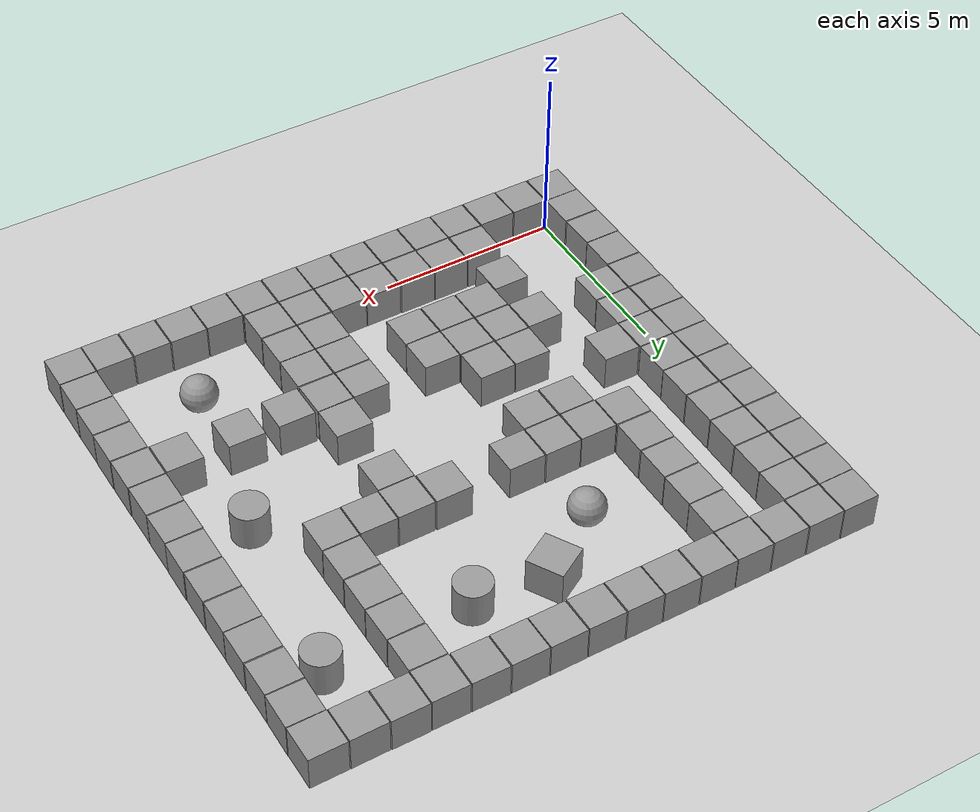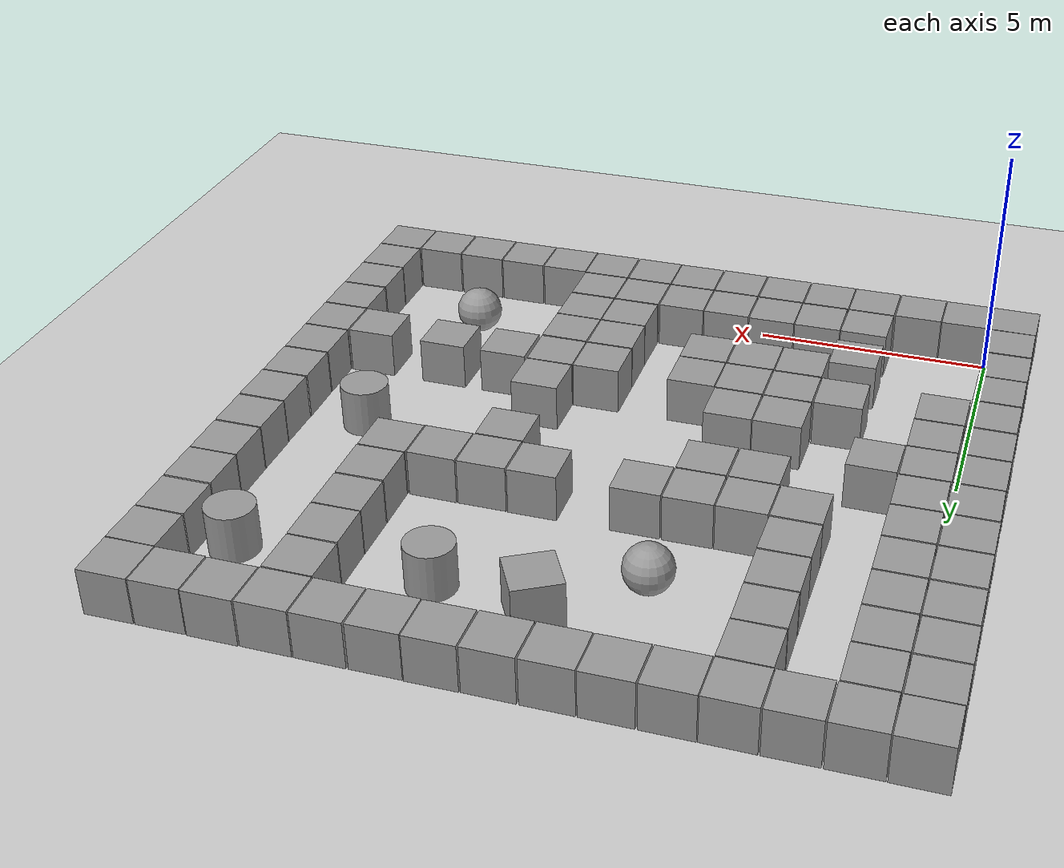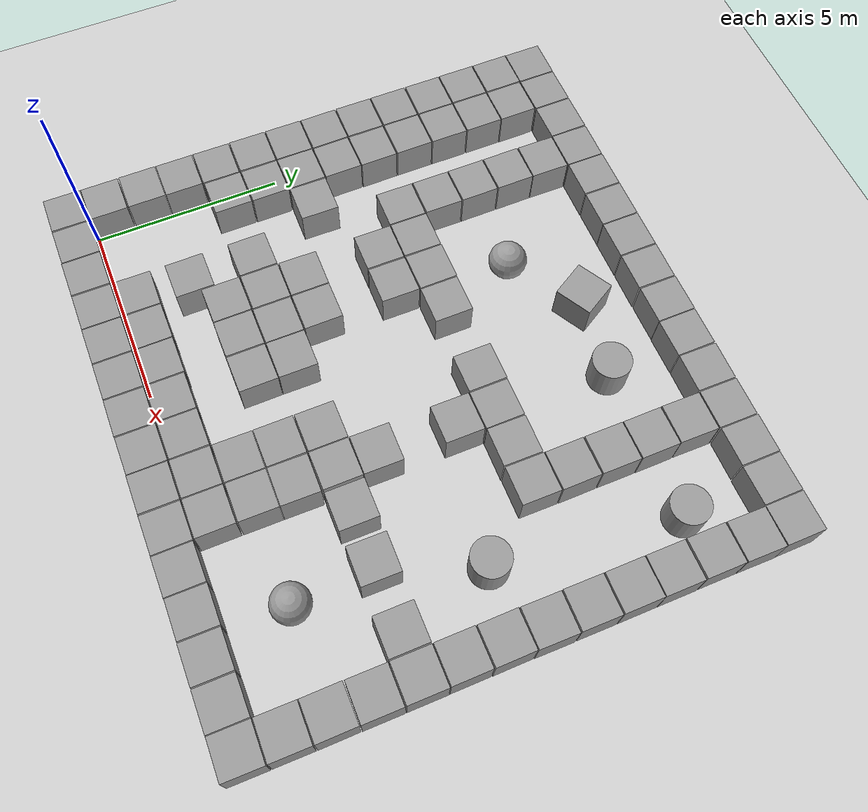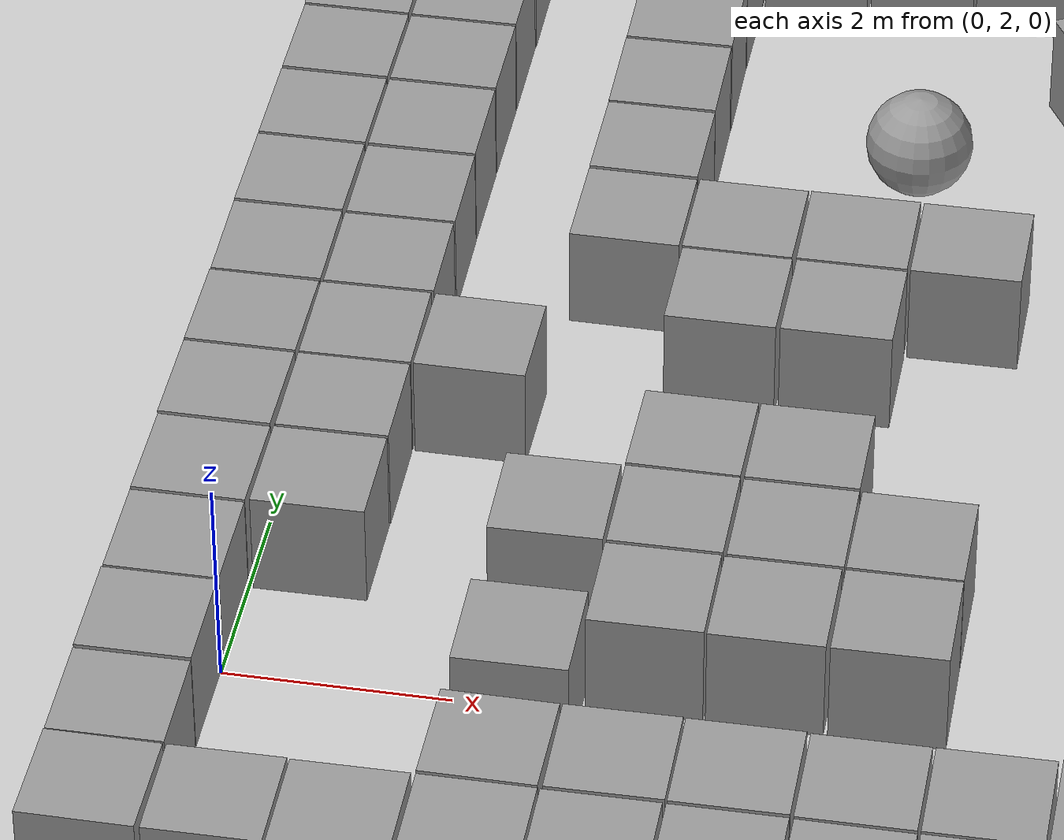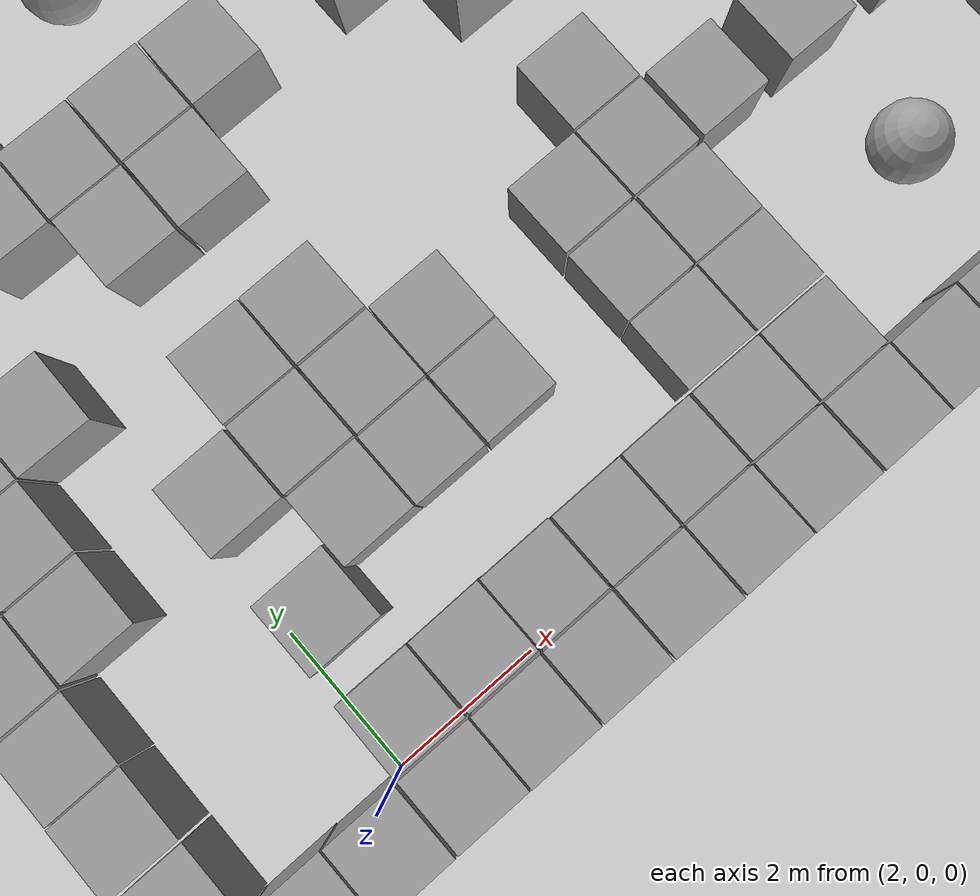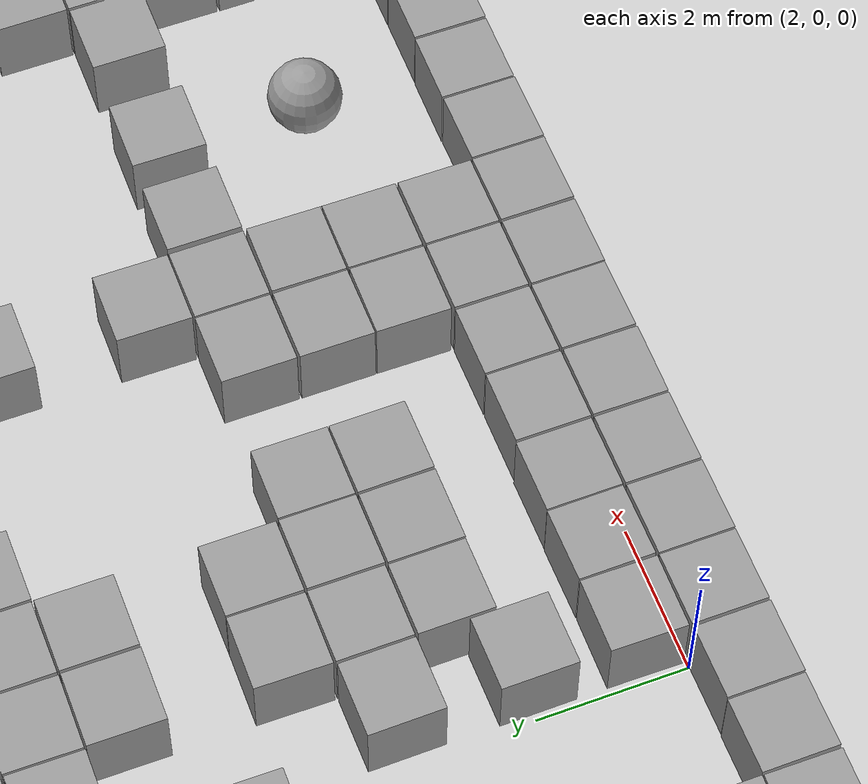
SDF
<?xml version="1.0"?>
<sdf version="1.6">
  <world name="hub_mix">
    <include><uri>model://ground_plane</uri></include>
    <include><uri>model://sun</uri></include>
    <physics type="ode"><real_time_update_rate>1000.0</real_time_update_rate><max_step_size>0.001</max_step_size><real_time_factor>1</real_time_factor><ode><solver><type>quick</type><iters>150</iters><precon_iters>0</precon_iters><sor>1.400000</sor><use_dynamic_moi_rescaling>1</use_dynamic_moi_rescaling></solver><constraints><cfm>0.00001</cfm><erp>0.2</erp><contact_max_correcting_vel>2000.000000</contact_max_correcting_vel><contact_surface_layer>0.01000</contact_surface_layer></constraints></ode></physics>
    <scene><shadows>false</shadows></scene>
    <gui fullscreen="0"><camera name="user_camera"><pose>6.7 -6 14 0 0.95 1.5707</pose><view_controller>orbit</view_controller><projection_type>perspective</projection_type></camera></gui>
    <model name='unit_box_0'>
      <pose>-0.5049 -0.4946 0.5 0 0 -0.00733</pose>
      <link name='link'><inertial><mass>1</mass><inertia><ixx>0.166667</ixx><ixy>0</ixy><ixz>0</ixz><iyy>0.166667</iyy><iyz>0</iyz><izz>0.166667</izz></inertia></inertial>
        <collision name='collision'><geometry><box><size>1 1 1</size></box></geometry><max_contacts>10</max_contacts></collision>
        <visual name='visual'><geometry><box><size>1 1 1</size></box></geometry><material><script><uri>file://media/materials/scripts/gazebo.material</uri><name>Gazebo/Grey</name></script></material></visual>
      </link>
    </model>
    <model name='unit_box_1'>
      <pose>0.5329 -0.4959 0.5 0 0 0.00518</pose>
      <link name='link'><inertial><mass>1</mass><inertia><ixx>0.166667</ixx><ixy>0</ixy><ixz>0</ixz><iyy>0.166667</iyy><iyz>0</iyz><izz>0.166667</izz></inertia></inertial>
        <collision name='collision'><geometry><box><size>1 1 1</size></box></geometry><max_contacts>10</max_contacts></collision>
        <visual name='visual'><geometry><box><size>1 1 1</size></box></geometry><material><script><uri>file://media/materials/scripts/gazebo.material</uri><name>Gazebo/Grey</name></script></material></visual>
      </link>
    </model>
    <model name='unit_box_2'>
      <pose>1.5576 -0.5018 0.5 0 0 0.00465</pose>
      <link name='link'><inertial><mass>1</mass><inertia><ixx>0.166667</ixx><ixy>0</ixy><ixz>0</ixz><iyy>0.166667</iyy><iyz>0</iyz><izz>0.166667</izz></inertia></inertial>
        <collision name='collision'><geometry><box><size>1 1 1</size></box></geometry><max_contacts>10</max_contacts></collision>
        <visual name='visual'><geometry><box><size>1 1 1</size></box></geometry><material><script><uri>file://media/materials/scripts/gazebo.material</uri><name>Gazebo/Grey</name></script></material></visual>
      </link>
    </model>
    <model name='unit_box_3'>
      <pose>2.5956 -0.4980 0.5 0 0 0.00085</pose>
      <link name='link'><inertial><mass>1</mass><inertia><ixx>0.166667</ixx><ixy>0</ixy><ixz>0</ixz><iyy>0.166667</iyy><iyz>0</iyz><izz>0.166667</izz></inertia></inertial>
        <collision name='collision'><geometry><box><size>1 1 1</size></box></geometry><max_contacts>10</max_contacts></collision>
        <visual name='visual'><geometry><box><size>1 1 1</size></box></geometry><material><script><uri>file://media/materials/scripts/gazebo.material</uri><name>Gazebo/Grey</name></script></material></visual>
      </link>
    </model>
    <model name='unit_box_4'>
      <pose>3.6187 -0.5011 0.5 0 0 0.00459</pose>
      <link name='link'><inertial><mass>1</mass><inertia><ixx>0.166667</ixx><ixy>0</ixy><ixz>0</ixz><iyy>0.166667</iyy><iyz>0</iyz><izz>0.166667</izz></inertia></inertial>
        <collision name='collision'><geometry><box><size>1 1 1</size></box></geometry><max_contacts>10</max_contacts></collision>
        <visual name='visual'><geometry><box><size>1 1 1</size></box></geometry><material><script><uri>file://media/materials/scripts/gazebo.material</uri><name>Gazebo/Grey</name></script></material></visual>
      </link>
    </model>
    <model name='unit_box_5'>
      <pose>4.6491 -0.4996 0.5 0 0 0.00274</pose>
      <link name='link'><inertial><mass>1</mass><inertia><ixx>0.166667</ixx><ixy>0</ixy><ixz>0</ixz><iyy>0.166667</iyy><iyz>0</iyz><izz>0.166667</izz></inertia></inertial>
        <collision name='collision'><geometry><box><size>1 1 1</size></box></geometry><max_contacts>10</max_contacts></collision>
        <visual name='visual'><geometry><box><size>1 1 1</size></box></geometry><material><script><uri>file://media/materials/scripts/gazebo.material</uri><name>Gazebo/Grey</name></script></material></visual>
      </link>
    </model>
    <model name='unit_box_6'>
      <pose>5.6816 -0.5055 0.5 0 0 -0.00564</pose>
      <link name='link'><inertial><mass>1</mass><inertia><ixx>0.166667</ixx><ixy>0</ixy><ixz>0</ixz><iyy>0.166667</iyy><iyz>0</iyz><izz>0.166667</izz></inertia></inertial>
        <collision name='collision'><geometry><box><size>1 1 1</size></box></geometry><max_contacts>10</max_contacts></collision>
        <visual name='visual'><geometry><box><size>1 1 1</size></box></geometry><material><script><uri>file://media/materials/scripts/gazebo.material</uri><name>Gazebo/Grey</name></script></material></visual>
      </link>
    </model>
    <model name='unit_box_7'>
      <pose>6.7125 -0.4992 0.5 0 0 0.00708</pose>
      <link name='link'><inertial><mass>1</mass><inertia><ixx>0.166667</ixx><ixy>0</ixy><ixz>0</ixz><iyy>0.166667</iyy><iyz>0</iyz><izz>0.166667</izz></inertia></inertial>
        <collision name='collision'><geometry><box><size>1 1 1</size></box></geometry><max_contacts>10</max_contacts></collision>
        <visual name='visual'><geometry><box><size>1 1 1</size></box></geometry><material><script><uri>file://media/materials/scripts/gazebo.material</uri><name>Gazebo/Grey</name></script></material></visual>
      </link>
    </model>
    <model name='unit_box_8'>
      <pose>7.7346 -0.5032 0.5 0 0 0.00004</pose>
      <link name='link'><inertial><mass>1</mass><inertia><ixx>0.166667</ixx><ixy>0</ixy><ixz>0</ixz><iyy>0.166667</iyy><iyz>0</iyz><izz>0.166667</izz></inertia></inertial>
        <collision name='collision'><geometry><box><size>1 1 1</size></box></geometry><max_contacts>10</max_contacts></collision>
        <visual name='visual'><geometry><box><size>1 1 1</size></box></geometry><material><script><uri>file://media/materials/scripts/gazebo.material</uri><name>Gazebo/Grey</name></script></material></visual>
      </link>
    </model>
    <model name='unit_box_9'>
      <pose>8.7730 -0.5037 0.5 0 0 0.00554</pose>
      <link name='link'><inertial><mass>1</mass><inertia><ixx>0.166667</ixx><ixy>0</ixy><ixz>0</ixz><iyy>0.166667</iyy><iyz>0</iyz><izz>0.166667</izz></inertia></inertial>
        <collision name='collision'><geometry><box><size>1 1 1</size></box></geometry><max_contacts>10</max_contacts></collision>
        <visual name='visual'><geometry><box><size>1 1 1</size></box></geometry><material><script><uri>file://media/materials/scripts/gazebo.material</uri><name>Gazebo/Grey</name></script></material></visual>
      </link>
    </model>
    <model name='unit_box_10'>
      <pose>9.7989 -0.5023 0.5 0 0 0.00690</pose>
      <link name='link'><inertial><mass>1</mass><inertia><ixx>0.166667</ixx><ixy>0</ixy><ixz>0</ixz><iyy>0.166667</iyy><iyz>0</iyz><izz>0.166667</izz></inertia></inertial>
        <collision name='collision'><geometry><box><size>1 1 1</size></box></geometry><max_contacts>10</max_contacts></collision>
        <visual name='visual'><geometry><box><size>1 1 1</size></box></geometry><material><script><uri>file://media/materials/scripts/gazebo.material</uri><name>Gazebo/Grey</name></script></material></visual>
      </link>
    </model>
    <model name='unit_box_11'>
      <pose>10.8253 -0.4948 0.5 0 0 -0.00397</pose>
      <link name='link'><inertial><mass>1</mass><inertia><ixx>0.166667</ixx><ixy>0</ixy><ixz>0</ixz><iyy>0.166667</iyy><iyz>0</iyz><izz>0.166667</izz></inertia></inertial>
        <collision name='collision'><geometry><box><size>1 1 1</size></box></geometry><max_contacts>10</max_contacts></collision>
        <visual name='visual'><geometry><box><size>1 1 1</size></box></geometry><material><script><uri>file://media/materials/scripts/gazebo.material</uri><name>Gazebo/Grey</name></script></material></visual>
      </link>
    </model>
    <model name='unit_box_12'>
      <pose>11.8583 -0.5036 0.5 0 0 -0.00067</pose>
      <link name='link'><inertial><mass>1</mass><inertia><ixx>0.166667</ixx><ixy>0</ixy><ixz>0</ixz><iyy>0.166667</iyy><iyz>0</iyz><izz>0.166667</izz></inertia></inertial>
        <collision name='collision'><geometry><box><size>1 1 1</size></box></geometry><max_contacts>10</max_contacts></collision>
        <visual name='visual'><geometry><box><size>1 1 1</size></box></geometry><material><script><uri>file://media/materials/scripts/gazebo.material</uri><name>Gazebo/Grey</name></script></material></visual>
      </link>
    </model>
    <model name='unit_box_13'>
      <pose>12.8941 -0.5033 0.5 0 0 0.00113</pose>
      <link name='link'><inertial><mass>1</mass><inertia><ixx>0.166667</ixx><ixy>0</ixy><ixz>0</ixz><iyy>0.166667</iyy><iyz>0</iyz><izz>0.166667</izz></inertia></inertial>
        <collision name='collision'><geometry><box><size>1 1 1</size></box></geometry><max_contacts>10</max_contacts></collision>
        <visual name='visual'><geometry><box><size>1 1 1</size></box></geometry><material><script><uri>file://media/materials/scripts/gazebo.material</uri><name>Gazebo/Grey</name></script></material></visual>
      </link>
    </model>
    <model name='unit_box_14'>
      <pose>13.9193 -0.5024 0.5 0 0 -0.00775</pose>
      <link name='link'><inertial><mass>1</mass><inertia><ixx>0.166667</ixx><ixy>0</ixy><ixz>0</ixz><iyy>0.166667</iyy><iyz>0</iyz><izz>0.166667</izz></inertia></inertial>
        <collision name='collision'><geometry><box><size>1 1 1</size></box></geometry><max_contacts>10</max_contacts></collision>
        <visual name='visual'><geometry><box><size>1 1 1</size></box></geometry><material><script><uri>file://media/materials/scripts/gazebo.material</uri><name>Gazebo/Grey</name></script></material></visual>
      </link>
    </model>
    <model name='unit_box_15'>
      <pose>-0.4976 12.8890 0.5 0 0 -0.00064</pose>
      <link name='link'><inertial><mass>1</mass><inertia><ixx>0.166667</ixx><ixy>0</ixy><ixz>0</ixz><iyy>0.166667</iyy><iyz>0</iyz><izz>0.166667</izz></inertia></inertial>
        <collision name='collision'><geometry><box><size>1 1 1</size></box></geometry><max_contacts>10</max_contacts></collision>
        <visual name='visual'><geometry><box><size>1 1 1</size></box></geometry><material><script><uri>file://media/materials/scripts/gazebo.material</uri><name>Gazebo/Grey</name></script></material></visual>
      </link>
    </model>
    <model name='unit_box_16'>
      <pose>0.5312 12.8853 0.5 0 0 0.00665</pose>
      <link name='link'><inertial><mass>1</mass><inertia><ixx>0.166667</ixx><ixy>0</ixy><ixz>0</ixz><iyy>0.166667</iyy><iyz>0</iyz><izz>0.166667</izz></inertia></inertial>
        <collision name='collision'><geometry><box><size>1 1 1</size></box></geometry><max_contacts>10</max_contacts></collision>
        <visual name='visual'><geometry><box><size>1 1 1</size></box></geometry><material><script><uri>file://media/materials/scripts/gazebo.material</uri><name>Gazebo/Grey</name></script></material></visual>
      </link>
    </model>
    <model name='unit_box_17'>
      <pose>1.5647 12.8871 0.5 0 0 0.00662</pose>
      <link name='link'><inertial><mass>1</mass><inertia><ixx>0.166667</ixx><ixy>0</ixy><ixz>0</ixz><iyy>0.166667</iyy><iyz>0</iyz><izz>0.166667</izz></inertia></inertial>
        <collision name='collision'><geometry><box><size>1 1 1</size></box></geometry><max_contacts>10</max_contacts></collision>
        <visual name='visual'><geometry><box><size>1 1 1</size></box></geometry><material><script><uri>file://media/materials/scripts/gazebo.material</uri><name>Gazebo/Grey</name></script></material></visual>
      </link>
    </model>
    <model name='unit_box_18'>
      <pose>2.5924 12.8876 0.5 0 0 -0.00482</pose>
      <link name='link'><inertial><mass>1</mass><inertia><ixx>0.166667</ixx><ixy>0</ixy><ixz>0</ixz><iyy>0.166667</iyy><iyz>0</iyz><izz>0.166667</izz></inertia></inertial>
        <collision name='collision'><geometry><box><size>1 1 1</size></box></geometry><max_contacts>10</max_contacts></collision>
        <visual name='visual'><geometry><box><size>1 1 1</size></box></geometry><material><script><uri>file://media/materials/scripts/gazebo.material</uri><name>Gazebo/Grey</name></script></material></visual>
      </link>
    </model>
    <model name='unit_box_19'>
      <pose>3.6150 12.8890 0.5 0 0 -0.00102</pose>
      <link name='link'><inertial><mass>1</mass><inertia><ixx>0.166667</ixx><ixy>0</ixy><ixz>0</ixz><iyy>0.166667</iyy><iyz>0</iyz><izz>0.166667</izz></inertia></inertial>
        <collision name='collision'><geometry><box><size>1 1 1</size></box></geometry><max_contacts>10</max_contacts></collision>
        <visual name='visual'><geometry><box><size>1 1 1</size></box></geometry><material><script><uri>file://media/materials/scripts/gazebo.material</uri><name>Gazebo/Grey</name></script></material></visual>
      </link>
    </model>
    <model name='unit_box_20'>
      <pose>4.6498 12.8898 0.5 0 0 0.00102</pose>
      <link name='link'><inertial><mass>1</mass><inertia><ixx>0.166667</ixx><ixy>0</ixy><ixz>0</ixz><iyy>0.166667</iyy><iyz>0</iyz><izz>0.166667</izz></inertia></inertial>
        <collision name='collision'><geometry><box><size>1 1 1</size></box></geometry><max_contacts>10</max_contacts></collision>
        <visual name='visual'><geometry><box><size>1 1 1</size></box></geometry><material><script><uri>file://media/materials/scripts/gazebo.material</uri><name>Gazebo/Grey</name></script></material></visual>
      </link>
    </model>
    <model name='unit_box_21'>
      <pose>5.6755 12.8867 0.5 0 0 0.00124</pose>
      <link name='link'><inertial><mass>1</mass><inertia><ixx>0.166667</ixx><ixy>0</ixy><ixz>0</ixz><iyy>0.166667</iyy><iyz>0</iyz><izz>0.166667</izz></inertia></inertial>
        <collision name='collision'><geometry><box><size>1 1 1</size></box></geometry><max_contacts>10</max_contacts></collision>
        <visual name='visual'><geometry><box><size>1 1 1</size></box></geometry><material><script><uri>file://media/materials/scripts/gazebo.material</uri><name>Gazebo/Grey</name></script></material></visual>
      </link>
    </model>
    <model name='unit_box_22'>
      <pose>6.7097 12.8861 0.5 0 0 -0.00467</pose>
      <link name='link'><inertial><mass>1</mass><inertia><ixx>0.166667</ixx><ixy>0</ixy><ixz>0</ixz><iyy>0.166667</iyy><iyz>0</iyz><izz>0.166667</izz></inertia></inertial>
        <collision name='collision'><geometry><box><size>1 1 1</size></box></geometry><max_contacts>10</max_contacts></collision>
        <visual name='visual'><geometry><box><size>1 1 1</size></box></geometry><material><script><uri>file://media/materials/scripts/gazebo.material</uri><name>Gazebo/Grey</name></script></material></visual>
      </link>
    </model>
    <model name='unit_box_23'>
      <pose>7.7457 12.8936 0.5 0 0 0.00475</pose>
      <link name='link'><inertial><mass>1</mass><inertia><ixx>0.166667</ixx><ixy>0</ixy><ixz>0</ixz><iyy>0.166667</iyy><iyz>0</iyz><izz>0.166667</izz></inertia></inertial>
        <collision name='collision'><geometry><box><size>1 1 1</size></box></geometry><max_contacts>10</max_contacts></collision>
        <visual name='visual'><geometry><box><size>1 1 1</size></box></geometry><material><script><uri>file://media/materials/scripts/gazebo.material</uri><name>Gazebo/Grey</name></script></material></visual>
      </link>
    </model>
    <model name='unit_box_24'>
      <pose>8.7683 12.8890 0.5 0 0 0.00429</pose>
      <link name='link'><inertial><mass>1</mass><inertia><ixx>0.166667</ixx><ixy>0</ixy><ixz>0</ixz><iyy>0.166667</iyy><iyz>0</iyz><izz>0.166667</izz></inertia></inertial>
        <collision name='collision'><geometry><box><size>1 1 1</size></box></geometry><max_contacts>10</max_contacts></collision>
        <visual name='visual'><geometry><box><size>1 1 1</size></box></geometry><material><script><uri>file://media/materials/scripts/gazebo.material</uri><name>Gazebo/Grey</name></script></material></visual>
      </link>
    </model>
    <model name='unit_box_25'>
      <pose>9.8007 12.8917 0.5 0 0 -0.00973</pose>
      <link name='link'><inertial><mass>1</mass><inertia><ixx>0.166667</ixx><ixy>0</ixy><ixz>0</ixz><iyy>0.166667</iyy><iyz>0</iyz><izz>0.166667</izz></inertia></inertial>
        <collision name='collision'><geometry><box><size>1 1 1</size></box></geometry><max_contacts>10</max_contacts></collision>
        <visual name='visual'><geometry><box><size>1 1 1</size></box></geometry><material><script><uri>file://media/materials/scripts/gazebo.material</uri><name>Gazebo/Grey</name></script></material></visual>
      </link>
    </model>
    <model name='unit_box_26'>
      <pose>10.8326 12.8864 0.5 0 0 -0.00361</pose>
      <link name='link'><inertial><mass>1</mass><inertia><ixx>0.166667</ixx><ixy>0</ixy><ixz>0</ixz><iyy>0.166667</iyy><iyz>0</iyz><izz>0.166667</izz></inertia></inertial>
        <collision name='collision'><geometry><box><size>1 1 1</size></box></geometry><max_contacts>10</max_contacts></collision>
        <visual name='visual'><geometry><box><size>1 1 1</size></box></geometry><material><script><uri>file://media/materials/scripts/gazebo.material</uri><name>Gazebo/Grey</name></script></material></visual>
      </link>
    </model>
    <model name='unit_box_27'>
      <pose>11.8604 12.8954 0.5 0 0 -0.00198</pose>
      <link name='link'><inertial><mass>1</mass><inertia><ixx>0.166667</ixx><ixy>0</ixy><ixz>0</ixz><iyy>0.166667</iyy><iyz>0</iyz><izz>0.166667</izz></inertia></inertial>
        <collision name='collision'><geometry><box><size>1 1 1</size></box></geometry><max_contacts>10</max_contacts></collision>
        <visual name='visual'><geometry><box><size>1 1 1</size></box></geometry><material><script><uri>file://media/materials/scripts/gazebo.material</uri><name>Gazebo/Grey</name></script></material></visual>
      </link>
    </model>
    <model name='unit_box_28'>
      <pose>12.8918 12.8865 0.5 0 0 0.00920</pose>
      <link name='link'><inertial><mass>1</mass><inertia><ixx>0.166667</ixx><ixy>0</ixy><ixz>0</ixz><iyy>0.166667</iyy><iyz>0</iyz><izz>0.166667</izz></inertia></inertial>
        <collision name='collision'><geometry><box><size>1 1 1</size></box></geometry><max_contacts>10</max_contacts></collision>
        <visual name='visual'><geometry><box><size>1 1 1</size></box></geometry><material><script><uri>file://media/materials/scripts/gazebo.material</uri><name>Gazebo/Grey</name></script></material></visual>
      </link>
    </model>
    <model name='unit_box_29'>
      <pose>13.9170 12.8905 0.5 0 0 0.00379</pose>
      <link name='link'><inertial><mass>1</mass><inertia><ixx>0.166667</ixx><ixy>0</ixy><ixz>0</ixz><iyy>0.166667</iyy><iyz>0</iyz><izz>0.166667</izz></inertia></inertial>
        <collision name='collision'><geometry><box><size>1 1 1</size></box></geometry><max_contacts>10</max_contacts></collision>
        <visual name='visual'><geometry><box><size>1 1 1</size></box></geometry><material><script><uri>file://media/materials/scripts/gazebo.material</uri><name>Gazebo/Grey</name></script></material></visual>
      </link>
    </model>
    <model name='unit_box_30'>
      <pose>-0.4976 0.5193 0.5 0 0 0.00308</pose>
      <link name='link'><inertial><mass>1</mass><inertia><ixx>0.166667</ixx><ixy>0</ixy><ixz>0</ixz><iyy>0.166667</iyy><iyz>0</iyz><izz>0.166667</izz></inertia></inertial>
        <collision name='collision'><geometry><box><size>1 1 1</size></box></geometry><max_contacts>10</max_contacts></collision>
        <visual name='visual'><geometry><box><size>1 1 1</size></box></geometry><material><script><uri>file://media/materials/scripts/gazebo.material</uri><name>Gazebo/Grey</name></script></material></visual>
      </link>
    </model>
    <model name='unit_box_31'>
      <pose>-0.5059 1.5576 0.5 0 0 0.00122</pose>
      <link name='link'><inertial><mass>1</mass><inertia><ixx>0.166667</ixx><ixy>0</ixy><ixz>0</ixz><iyy>0.166667</iyy><iyz>0</iyz><izz>0.166667</izz></inertia></inertial>
        <collision name='collision'><geometry><box><size>1 1 1</size></box></geometry><max_contacts>10</max_contacts></collision>
        <visual name='visual'><geometry><box><size>1 1 1</size></box></geometry><material><script><uri>file://media/materials/scripts/gazebo.material</uri><name>Gazebo/Grey</name></script></material></visual>
      </link>
    </model>
    <model name='unit_box_32'>
      <pose>-0.4989 2.5807 0.5 0 0 -0.00042</pose>
      <link name='link'><inertial><mass>1</mass><inertia><ixx>0.166667</ixx><ixy>0</ixy><ixz>0</ixz><iyy>0.166667</iyy><iyz>0</iyz><izz>0.166667</izz></inertia></inertial>
        <collision name='collision'><geometry><box><size>1 1 1</size></box></geometry><max_contacts>10</max_contacts></collision>
        <visual name='visual'><geometry><box><size>1 1 1</size></box></geometry><material><script><uri>file://media/materials/scripts/gazebo.material</uri><name>Gazebo/Grey</name></script></material></visual>
      </link>
    </model>
    <model name='unit_box_33'>
      <pose>-0.4983 3.6144 0.5 0 0 -0.00793</pose>
      <link name='link'><inertial><mass>1</mass><inertia><ixx>0.166667</ixx><ixy>0</ixy><ixz>0</ixz><iyy>0.166667</iyy><iyz>0</iyz><izz>0.166667</izz></inertia></inertial>
        <collision name='collision'><geometry><box><size>1 1 1</size></box></geometry><max_contacts>10</max_contacts></collision>
        <visual name='visual'><geometry><box><size>1 1 1</size></box></geometry><material><script><uri>file://media/materials/scripts/gazebo.material</uri><name>Gazebo/Grey</name></script></material></visual>
      </link>
    </model>
    <model name='unit_box_34'>
      <pose>-0.5036 4.6518 0.5 0 0 -0.00616</pose>
      <link name='link'><inertial><mass>1</mass><inertia><ixx>0.166667</ixx><ixy>0</ixy><ixz>0</ixz><iyy>0.166667</iyy><iyz>0</iyz><izz>0.166667</izz></inertia></inertial>
        <collision name='collision'><geometry><box><size>1 1 1</size></box></geometry><max_contacts>10</max_contacts></collision>
        <visual name='visual'><geometry><box><size>1 1 1</size></box></geometry><material><script><uri>file://media/materials/scripts/gazebo.material</uri><name>Gazebo/Grey</name></script></material></visual>
      </link>
    </model>
    <model name='unit_box_35'>
      <pose>-0.4998 5.6816 0.5 0 0 -0.00584</pose>
      <link name='link'><inertial><mass>1</mass><inertia><ixx>0.166667</ixx><ixy>0</ixy><ixz>0</ixz><iyy>0.166667</iyy><iyz>0</iyz><izz>0.166667</izz></inertia></inertial>
        <collision name='collision'><geometry><box><size>1 1 1</size></box></geometry><max_contacts>10</max_contacts></collision>
        <visual name='visual'><geometry><box><size>1 1 1</size></box></geometry><material><script><uri>file://media/materials/scripts/gazebo.material</uri><name>Gazebo/Grey</name></script></material></visual>
      </link>
    </model>
    <model name='unit_box_36'>
      <pose>-0.4963 6.7106 0.5 0 0 0.00936</pose>
      <link name='link'><inertial><mass>1</mass><inertia><ixx>0.166667</ixx><ixy>0</ixy><ixz>0</ixz><iyy>0.166667</iyy><iyz>0</iyz><izz>0.166667</izz></inertia></inertial>
        <collision name='collision'><geometry><box><size>1 1 1</size></box></geometry><max_contacts>10</max_contacts></collision>
        <visual name='visual'><geometry><box><size>1 1 1</size></box></geometry><material><script><uri>file://media/materials/scripts/gazebo.material</uri><name>Gazebo/Grey</name></script></material></visual>
      </link>
    </model>
    <model name='unit_box_37'>
      <pose>-0.5035 7.7418 0.5 0 0 -0.00288</pose>
      <link name='link'><inertial><mass>1</mass><inertia><ixx>0.166667</ixx><ixy>0</ixy><ixz>0</ixz><iyy>0.166667</iyy><iyz>0</iyz><izz>0.166667</izz></inertia></inertial>
        <collision name='collision'><geometry><box><size>1 1 1</size></box></geometry><max_contacts>10</max_contacts></collision>
        <visual name='visual'><geometry><box><size>1 1 1</size></box></geometry><material><script><uri>file://media/materials/scripts/gazebo.material</uri><name>Gazebo/Grey</name></script></material></visual>
      </link>
    </model>
    <model name='unit_box_38'>
      <pose>-0.5027 8.7737 0.5 0 0 -0.00153</pose>
      <link name='link'><inertial><mass>1</mass><inertia><ixx>0.166667</ixx><ixy>0</ixy><ixz>0</ixz><iyy>0.166667</iyy><iyz>0</iyz><izz>0.166667</izz></inertia></inertial>
        <collision name='collision'><geometry><box><size>1 1 1</size></box></geometry><max_contacts>10</max_contacts></collision>
        <visual name='visual'><geometry><box><size>1 1 1</size></box></geometry><material><script><uri>file://media/materials/scripts/gazebo.material</uri><name>Gazebo/Grey</name></script></material></visual>
      </link>
    </model>
    <model name='unit_box_39'>
      <pose>-0.5013 9.8108 0.5 0 0 -0.00366</pose>
      <link name='link'><inertial><mass>1</mass><inertia><ixx>0.166667</ixx><ixy>0</ixy><ixz>0</ixz><iyy>0.166667</iyy><iyz>0</iyz><izz>0.166667</izz></inertia></inertial>
        <collision name='collision'><geometry><box><size>1 1 1</size></box></geometry><max_contacts>10</max_contacts></collision>
        <visual name='visual'><geometry><box><size>1 1 1</size></box></geometry><material><script><uri>file://media/materials/scripts/gazebo.material</uri><name>Gazebo/Grey</name></script></material></visual>
      </link>
    </model>
    <model name='unit_box_40'>
      <pose>-0.5053 10.8412 0.5 0 0 -0.00137</pose>
      <link name='link'><inertial><mass>1</mass><inertia><ixx>0.166667</ixx><ixy>0</ixy><ixz>0</ixz><iyy>0.166667</iyy><iyz>0</iyz><izz>0.166667</izz></inertia></inertial>
        <collision name='collision'><geometry><box><size>1 1 1</size></box></geometry><max_contacts>10</max_contacts></collision>
        <visual name='visual'><geometry><box><size>1 1 1</size></box></geometry><material><script><uri>file://media/materials/scripts/gazebo.material</uri><name>Gazebo/Grey</name></script></material></visual>
      </link>
    </model>
    <model name='unit_box_41'>
      <pose>-0.5057 11.8731 0.5 0 0 0.00473</pose>
      <link name='link'><inertial><mass>1</mass><inertia><ixx>0.166667</ixx><ixy>0</ixy><ixz>0</ixz><iyy>0.166667</iyy><iyz>0</iyz><izz>0.166667</izz></inertia></inertial>
        <collision name='collision'><geometry><box><size>1 1 1</size></box></geometry><max_contacts>10</max_contacts></collision>
        <visual name='visual'><geometry><box><size>1 1 1</size></box></geometry><material><script><uri>file://media/materials/scripts/gazebo.material</uri><name>Gazebo/Grey</name></script></material></visual>
      </link>
    </model>
    <model name='unit_box_42'>
      <pose>13.9219 0.5238 0.5 0 0 -0.00483</pose>
      <link name='link'><inertial><mass>1</mass><inertia><ixx>0.166667</ixx><ixy>0</ixy><ixz>0</ixz><iyy>0.166667</iyy><iyz>0</iyz><izz>0.166667</izz></inertia></inertial>
        <collision name='collision'><geometry><box><size>1 1 1</size></box></geometry><max_contacts>10</max_contacts></collision>
        <visual name='visual'><geometry><box><size>1 1 1</size></box></geometry><material><script><uri>file://media/materials/scripts/gazebo.material</uri><name>Gazebo/Grey</name></script></material></visual>
      </link>
    </model>
    <model name='unit_box_43'>
      <pose>13.9241 1.5502 0.5 0 0 0.00752</pose>
      <link name='link'><inertial><mass>1</mass><inertia><ixx>0.166667</ixx><ixy>0</ixy><ixz>0</ixz><iyy>0.166667</iyy><iyz>0</iyz><izz>0.166667</izz></inertia></inertial>
        <collision name='collision'><geometry><box><size>1 1 1</size></box></geometry><max_contacts>10</max_contacts></collision>
        <visual name='visual'><geometry><box><size>1 1 1</size></box></geometry><material><script><uri>file://media/materials/scripts/gazebo.material</uri><name>Gazebo/Grey</name></script></material></visual>
      </link>
    </model>
    <model name='unit_box_44'>
      <pose>13.9260 2.5843 0.5 0 0 -0.00164</pose>
      <link name='link'><inertial><mass>1</mass><inertia><ixx>0.166667</ixx><ixy>0</ixy><ixz>0</ixz><iyy>0.166667</iyy><iyz>0</iyz><izz>0.166667</izz></inertia></inertial>
        <collision name='collision'><geometry><box><size>1 1 1</size></box></geometry><max_contacts>10</max_contacts></collision>
        <visual name='visual'><geometry><box><size>1 1 1</size></box></geometry><material><script><uri>file://media/materials/scripts/gazebo.material</uri><name>Gazebo/Grey</name></script></material></visual>
      </link>
    </model>
    <model name='unit_box_45'>
      <pose>13.9228 3.6181 0.5 0 0 0.00011</pose>
      <link name='link'><inertial><mass>1</mass><inertia><ixx>0.166667</ixx><ixy>0</ixy><ixz>0</ixz><iyy>0.166667</iyy><iyz>0</iyz><izz>0.166667</izz></inertia></inertial>
        <collision name='collision'><geometry><box><size>1 1 1</size></box></geometry><max_contacts>10</max_contacts></collision>
        <visual name='visual'><geometry><box><size>1 1 1</size></box></geometry><material><script><uri>file://media/materials/scripts/gazebo.material</uri><name>Gazebo/Grey</name></script></material></visual>
      </link>
    </model>
    <model name='unit_box_46'>
      <pose>13.9150 4.6455 0.5 0 0 0.00378</pose>
      <link name='link'><inertial><mass>1</mass><inertia><ixx>0.166667</ixx><ixy>0</ixy><ixz>0</ixz><iyy>0.166667</iyy><iyz>0</iyz><izz>0.166667</izz></inertia></inertial>
        <collision name='collision'><geometry><box><size>1 1 1</size></box></geometry><max_contacts>10</max_contacts></collision>
        <visual name='visual'><geometry><box><size>1 1 1</size></box></geometry><material><script><uri>file://media/materials/scripts/gazebo.material</uri><name>Gazebo/Grey</name></script></material></visual>
      </link>
    </model>
    <model name='unit_box_47'>
      <pose>13.9142 5.6780 0.5 0 0 0.00872</pose>
      <link name='link'><inertial><mass>1</mass><inertia><ixx>0.166667</ixx><ixy>0</ixy><ixz>0</ixz><iyy>0.166667</iyy><iyz>0</iyz><izz>0.166667</izz></inertia></inertial>
        <collision name='collision'><geometry><box><size>1 1 1</size></box></geometry><max_contacts>10</max_contacts></collision>
        <visual name='visual'><geometry><box><size>1 1 1</size></box></geometry><material><script><uri>file://media/materials/scripts/gazebo.material</uri><name>Gazebo/Grey</name></script></material></visual>
      </link>
    </model>
    <model name='unit_box_48'>
      <pose>13.9226 6.7080 0.5 0 0 -0.00763</pose>
      <link name='link'><inertial><mass>1</mass><inertia><ixx>0.166667</ixx><ixy>0</ixy><ixz>0</ixz><iyy>0.166667</iyy><iyz>0</iyz><izz>0.166667</izz></inertia></inertial>
        <collision name='collision'><geometry><box><size>1 1 1</size></box></geometry><max_contacts>10</max_contacts></collision>
        <visual name='visual'><geometry><box><size>1 1 1</size></box></geometry><material><script><uri>file://media/materials/scripts/gazebo.material</uri><name>Gazebo/Grey</name></script></material></visual>
      </link>
    </model>
    <model name='unit_box_49'>
      <pose>13.9209 7.7441 0.5 0 0 -0.00447</pose>
      <link name='link'><inertial><mass>1</mass><inertia><ixx>0.166667</ixx><ixy>0</ixy><ixz>0</ixz><iyy>0.166667</iyy><iyz>0</iyz><izz>0.166667</izz></inertia></inertial>
        <collision name='collision'><geometry><box><size>1 1 1</size></box></geometry><max_contacts>10</max_contacts></collision>
        <visual name='visual'><geometry><box><size>1 1 1</size></box></geometry><material><script><uri>file://media/materials/scripts/gazebo.material</uri><name>Gazebo/Grey</name></script></material></visual>
      </link>
    </model>
    <model name='unit_box_50'>
      <pose>13.9202 8.7804 0.5 0 0 0.00314</pose>
      <link name='link'><inertial><mass>1</mass><inertia><ixx>0.166667</ixx><ixy>0</ixy><ixz>0</ixz><iyy>0.166667</iyy><iyz>0</iyz><izz>0.166667</izz></inertia></inertial>
        <collision name='collision'><geometry><box><size>1 1 1</size></box></geometry><max_contacts>10</max_contacts></collision>
        <visual name='visual'><geometry><box><size>1 1 1</size></box></geometry><material><script><uri>file://media/materials/scripts/gazebo.material</uri><name>Gazebo/Grey</name></script></material></visual>
      </link>
    </model>
    <model name='unit_box_51'>
      <pose>13.9205 9.8011 0.5 0 0 -0.00054</pose>
      <link name='link'><inertial><mass>1</mass><inertia><ixx>0.166667</ixx><ixy>0</ixy><ixz>0</ixz><iyy>0.166667</iyy><iyz>0</iyz><izz>0.166667</izz></inertia></inertial>
        <collision name='collision'><geometry><box><size>1 1 1</size></box></geometry><max_contacts>10</max_contacts></collision>
        <visual name='visual'><geometry><box><size>1 1 1</size></box></geometry><material><script><uri>file://media/materials/scripts/gazebo.material</uri><name>Gazebo/Grey</name></script></material></visual>
      </link>
    </model>
    <model name='unit_box_52'>
      <pose>13.9143 10.8437 0.5 0 0 0.00036</pose>
      <link name='link'><inertial><mass>1</mass><inertia><ixx>0.166667</ixx><ixy>0</ixy><ixz>0</ixz><iyy>0.166667</iyy><iyz>0</iyz><izz>0.166667</izz></inertia></inertial>
        <collision name='collision'><geometry><box><size>1 1 1</size></box></geometry><max_contacts>10</max_contacts></collision>
        <visual name='visual'><geometry><box><size>1 1 1</size></box></geometry><material><script><uri>file://media/materials/scripts/gazebo.material</uri><name>Gazebo/Grey</name></script></material></visual>
      </link>
    </model>
    <model name='unit_box_53'>
      <pose>13.9212 11.8722 0.5 0 0 -0.00963</pose>
      <link name='link'><inertial><mass>1</mass><inertia><ixx>0.166667</ixx><ixy>0</ixy><ixz>0</ixz><iyy>0.166667</iyy><iyz>0</iyz><izz>0.166667</izz></inertia></inertial>
        <collision name='collision'><geometry><box><size>1 1 1</size></box></geometry><max_contacts>10</max_contacts></collision>
        <visual name='visual'><geometry><box><size>1 1 1</size></box></geometry><material><script><uri>file://media/materials/scripts/gazebo.material</uri><name>Gazebo/Grey</name></script></material></visual>
      </link>
    </model>
    <model name='unit_box_54'>
      <pose>2.5939 0.5324 0.5 0 0 -0.00897</pose>
      <link name='link'><inertial><mass>1</mass><inertia><ixx>0.166667</ixx><ixy>0</ixy><ixz>0</ixz><iyy>0.166667</iyy><iyz>0</iyz><izz>0.166667</izz></inertia></inertial>
        <collision name='collision'><geometry><box><size>1 1 1</size></box></geometry><max_contacts>10</max_contacts></collision>
        <visual name='visual'><geometry><box><size>1 1 1</size></box></geometry><material><script><uri>file://media/materials/scripts/gazebo.material</uri><name>Gazebo/Grey</name></script></material></visual>
      </link>
    </model>
    <model name='unit_box_55'>
      <pose>3.6250 0.5344 0.5 0 0 0.01027</pose>
      <link name='link'><inertial><mass>1</mass><inertia><ixx>0.166667</ixx><ixy>0</ixy><ixz>0</ixz><iyy>0.166667</iyy><iyz>0</iyz><izz>0.166667</izz></inertia></inertial>
        <collision name='collision'><geometry><box><size>1 1 1</size></box></geometry><max_contacts>10</max_contacts></collision>
        <visual name='visual'><geometry><box><size>1 1 1</size></box></geometry><material><script><uri>file://media/materials/scripts/gazebo.material</uri><name>Gazebo/Grey</name></script></material></visual>
      </link>
    </model>
    <model name='unit_box_56'>
      <pose>4.6451 0.5350 0.5 0 0 0.00585</pose>
      <link name='link'><inertial><mass>1</mass><inertia><ixx>0.166667</ixx><ixy>0</ixy><ixz>0</ixz><iyy>0.166667</iyy><iyz>0</iyz><izz>0.166667</izz></inertia></inertial>
        <collision name='collision'><geometry><box><size>1 1 1</size></box></geometry><max_contacts>10</max_contacts></collision>
        <visual name='visual'><geometry><box><size>1 1 1</size></box></geometry><material><script><uri>file://media/materials/scripts/gazebo.material</uri><name>Gazebo/Grey</name></script></material></visual>
      </link>
    </model>
    <model name='unit_box_57'>
      <pose>5.6771 0.5250 0.5 0 0 0.00370</pose>
      <link name='link'><inertial><mass>1</mass><inertia><ixx>0.166667</ixx><ixy>0</ixy><ixz>0</ixz><iyy>0.166667</iyy><iyz>0</iyz><izz>0.166667</izz></inertia></inertial>
        <collision name='collision'><geometry><box><size>1 1 1</size></box></geometry><max_contacts>10</max_contacts></collision>
        <visual name='visual'><geometry><box><size>1 1 1</size></box></geometry><material><script><uri>file://media/materials/scripts/gazebo.material</uri><name>Gazebo/Grey</name></script></material></visual>
      </link>
    </model>
    <model name='unit_box_58'>
      <pose>6.7048 0.5306 0.5 0 0 0.00640</pose>
      <link name='link'><inertial><mass>1</mass><inertia><ixx>0.166667</ixx><ixy>0</ixy><ixz>0</ixz><iyy>0.166667</iyy><iyz>0</iyz><izz>0.166667</izz></inertia></inertial>
        <collision name='collision'><geometry><box><size>1 1 1</size></box></geometry><max_contacts>10</max_contacts></collision>
        <visual name='visual'><geometry><box><size>1 1 1</size></box></geometry><material><script><uri>file://media/materials/scripts/gazebo.material</uri><name>Gazebo/Grey</name></script></material></visual>
      </link>
    </model>
    <model name='unit_box_59'>
      <pose>7.7388 0.5280 0.5 0 0 -0.00174</pose>
      <link name='link'><inertial><mass>1</mass><inertia><ixx>0.166667</ixx><ixy>0</ixy><ixz>0</ixz><iyy>0.166667</iyy><iyz>0</iyz><izz>0.166667</izz></inertia></inertial>
        <collision name='collision'><geometry><box><size>1 1 1</size></box></geometry><max_contacts>10</max_contacts></collision>
        <visual name='visual'><geometry><box><size>1 1 1</size></box></geometry><material><script><uri>file://media/materials/scripts/gazebo.material</uri><name>Gazebo/Grey</name></script></material></visual>
      </link>
    </model>
    <model name='unit_box_60'>
      <pose>8.7654 0.5247 0.5 0 0 0.00135</pose>
      <link name='link'><inertial><mass>1</mass><inertia><ixx>0.166667</ixx><ixy>0</ixy><ixz>0</ixz><iyy>0.166667</iyy><iyz>0</iyz><izz>0.166667</izz></inertia></inertial>
        <collision name='collision'><geometry><box><size>1 1 1</size></box></geometry><max_contacts>10</max_contacts></collision>
        <visual name='visual'><geometry><box><size>1 1 1</size></box></geometry><material><script><uri>file://media/materials/scripts/gazebo.material</uri><name>Gazebo/Grey</name></script></material></visual>
      </link>
    </model>
    <model name='unit_box_61'>
      <pose>7.7438 1.5659 0.5 0 0 -0.00829</pose>
      <link name='link'><inertial><mass>1</mass><inertia><ixx>0.166667</ixx><ixy>0</ixy><ixz>0</ixz><iyy>0.166667</iyy><iyz>0</iyz><izz>0.166667</izz></inertia></inertial>
        <collision name='collision'><geometry><box><size>1 1 1</size></box></geometry><max_contacts>10</max_contacts></collision>
        <visual name='visual'><geometry><box><size>1 1 1</size></box></geometry><material><script><uri>file://media/materials/scripts/gazebo.material</uri><name>Gazebo/Grey</name></script></material></visual>
      </link>
    </model>
    <model name='unit_box_62'>
      <pose>8.7676 1.5638 0.5 0 0 -0.00436</pose>
      <link name='link'><inertial><mass>1</mass><inertia><ixx>0.166667</ixx><ixy>0</ixy><ixz>0</ixz><iyy>0.166667</iyy><iyz>0</iyz><izz>0.166667</izz></inertia></inertial>
        <collision name='collision'><geometry><box><size>1 1 1</size></box></geometry><max_contacts>10</max_contacts></collision>
        <visual name='visual'><geometry><box><size>1 1 1</size></box></geometry><material><script><uri>file://media/materials/scripts/gazebo.material</uri><name>Gazebo/Grey</name></script></material></visual>
      </link>
    </model>
    <model name='unit_box_63'>
      <pose>2.5932 1.9353 0.5 0 0 0.00752</pose>
      <link name='link'><inertial><mass>1</mass><inertia><ixx>0.166667</ixx><ixy>0</ixy><ixz>0</ixz><iyy>0.166667</iyy><iyz>0</iyz><izz>0.166667</izz></inertia></inertial>
        <collision name='collision'><geometry><box><size>1 1 1</size></box></geometry><max_contacts>10</max_contacts></collision>
        <visual name='visual'><geometry><box><size>1 1 1</size></box></geometry><material><script><uri>file://media/materials/scripts/gazebo.material</uri><name>Gazebo/Grey</name></script></material></visual>
      </link>
    </model>
    <model name='unit_box_64'>
      <pose>3.6215 2.5927 0.5 0 0 0.00748</pose>
      <link name='link'><inertial><mass>1</mass><inertia><ixx>0.166667</ixx><ixy>0</ixy><ixz>0</ixz><iyy>0.166667</iyy><iyz>0</iyz><izz>0.166667</izz></inertia></inertial>
        <collision name='collision'><geometry><box><size>1 1 1</size></box></geometry><max_contacts>10</max_contacts></collision>
        <visual name='visual'><geometry><box><size>1 1 1</size></box></geometry><material><script><uri>file://media/materials/scripts/gazebo.material</uri><name>Gazebo/Grey</name></script></material></visual>
      </link>
    </model>
    <model name='unit_box_65'>
      <pose>4.6457 2.5880 0.5 0 0 0.00490</pose>
      <link name='link'><inertial><mass>1</mass><inertia><ixx>0.166667</ixx><ixy>0</ixy><ixz>0</ixz><iyy>0.166667</iyy><iyz>0</iyz><izz>0.166667</izz></inertia></inertial>
        <collision name='collision'><geometry><box><size>1 1 1</size></box></geometry><max_contacts>10</max_contacts></collision>
        <visual name='visual'><geometry><box><size>1 1 1</size></box></geometry><material><script><uri>file://media/materials/scripts/gazebo.material</uri><name>Gazebo/Grey</name></script></material></visual>
      </link>
    </model>
    <model name='unit_box_66'>
      <pose>5.6797 2.5932 0.5 0 0 0.00994</pose>
      <link name='link'><inertial><mass>1</mass><inertia><ixx>0.166667</ixx><ixy>0</ixy><ixz>0</ixz><iyy>0.166667</iyy><iyz>0</iyz><izz>0.166667</izz></inertia></inertial>
        <collision name='collision'><geometry><box><size>1 1 1</size></box></geometry><max_contacts>10</max_contacts></collision>
        <visual name='visual'><geometry><box><size>1 1 1</size></box></geometry><material><script><uri>file://media/materials/scripts/gazebo.material</uri><name>Gazebo/Grey</name></script></material></visual>
      </link>
    </model>
    <model name='unit_box_67'>
      <pose>7.7427 2.5911 0.5 0 0 0.00468</pose>
      <link name='link'><inertial><mass>1</mass><inertia><ixx>0.166667</ixx><ixy>0</ixy><ixz>0</ixz><iyy>0.166667</iyy><iyz>0</iyz><izz>0.166667</izz></inertia></inertial>
        <collision name='collision'><geometry><box><size>1 1 1</size></box></geometry><max_contacts>10</max_contacts></collision>
        <visual name='visual'><geometry><box><size>1 1 1</size></box></geometry><material><script><uri>file://media/materials/scripts/gazebo.material</uri><name>Gazebo/Grey</name></script></material></visual>
      </link>
    </model>
    <model name='unit_box_68'>
      <pose>8.7751 2.5852 0.5 0 0 -0.00948</pose>
      <link name='link'><inertial><mass>1</mass><inertia><ixx>0.166667</ixx><ixy>0</ixy><ixz>0</ixz><iyy>0.166667</iyy><iyz>0</iyz><izz>0.166667</izz></inertia></inertial>
        <collision name='collision'><geometry><box><size>1 1 1</size></box></geometry><max_contacts>10</max_contacts></collision>
        <visual name='visual'><geometry><box><size>1 1 1</size></box></geometry><material><script><uri>file://media/materials/scripts/gazebo.material</uri><name>Gazebo/Grey</name></script></material></visual>
      </link>
    </model>
    <model name='unit_box_69'>
      <pose>0.5335 3.6242 0.5 0 0 0.00332</pose>
      <link name='link'><inertial><mass>1</mass><inertia><ixx>0.166667</ixx><ixy>0</ixy><ixz>0</ixz><iyy>0.166667</iyy><iyz>0</iyz><izz>0.166667</izz></inertia></inertial>
        <collision name='collision'><geometry><box><size>1 1 1</size></box></geometry><max_contacts>10</max_contacts></collision>
        <visual name='visual'><geometry><box><size>1 1 1</size></box></geometry><material><script><uri>file://media/materials/scripts/gazebo.material</uri><name>Gazebo/Grey</name></script></material></visual>
      </link>
    </model>
    <model name='unit_box_70'>
      <pose>2.5895 3.6172 0.5 0 0 0.01014</pose>
      <link name='link'><inertial><mass>1</mass><inertia><ixx>0.166667</ixx><ixy>0</ixy><ixz>0</ixz><iyy>0.166667</iyy><iyz>0</iyz><izz>0.166667</izz></inertia></inertial>
        <collision name='collision'><geometry><box><size>1 1 1</size></box></geometry><max_contacts>10</max_contacts></collision>
        <visual name='visual'><geometry><box><size>1 1 1</size></box></geometry><material><script><uri>file://media/materials/scripts/gazebo.material</uri><name>Gazebo/Grey</name></script></material></visual>
      </link>
    </model>
    <model name='unit_box_71'>
      <pose>3.6225 3.6258 0.5 0 0 0.00336</pose>
      <link name='link'><inertial><mass>1</mass><inertia><ixx>0.166667</ixx><ixy>0</ixy><ixz>0</ixz><iyy>0.166667</iyy><iyz>0</iyz><izz>0.166667</izz></inertia></inertial>
        <collision name='collision'><geometry><box><size>1 1 1</size></box></geometry><max_contacts>10</max_contacts></collision>
        <visual name='visual'><geometry><box><size>1 1 1</size></box></geometry><material><script><uri>file://media/materials/scripts/gazebo.material</uri><name>Gazebo/Grey</name></script></material></visual>
      </link>
    </model>
    <model name='unit_box_72'>
      <pose>4.6543 3.6168 0.5 0 0 0.00464</pose>
      <link name='link'><inertial><mass>1</mass><inertia><ixx>0.166667</ixx><ixy>0</ixy><ixz>0</ixz><iyy>0.166667</iyy><iyz>0</iyz><izz>0.166667</izz></inertia></inertial>
        <collision name='collision'><geometry><box><size>1 1 1</size></box></geometry><max_contacts>10</max_contacts></collision>
        <visual name='visual'><geometry><box><size>1 1 1</size></box></geometry><material><script><uri>file://media/materials/scripts/gazebo.material</uri><name>Gazebo/Grey</name></script></material></visual>
      </link>
    </model>
    <model name='unit_box_73'>
      <pose>5.6752 3.6179 0.5 0 0 -0.00108</pose>
      <link name='link'><inertial><mass>1</mass><inertia><ixx>0.166667</ixx><ixy>0</ixy><ixz>0</ixz><iyy>0.166667</iyy><iyz>0</iyz><izz>0.166667</izz></inertia></inertial>
        <collision name='collision'><geometry><box><size>1 1 1</size></box></geometry><max_contacts>10</max_contacts></collision>
        <visual name='visual'><geometry><box><size>1 1 1</size></box></geometry><material><script><uri>file://media/materials/scripts/gazebo.material</uri><name>Gazebo/Grey</name></script></material></visual>
      </link>
    </model>
    <model name='unit_box_74'>
      <pose>7.7403 3.6259 0.5 0 0 0.00272</pose>
      <link name='link'><inertial><mass>1</mass><inertia><ixx>0.166667</ixx><ixy>0</ixy><ixz>0</ixz><iyy>0.166667</iyy><iyz>0</iyz><izz>0.166667</izz></inertia></inertial>
        <collision name='collision'><geometry><box><size>1 1 1</size></box></geometry><max_contacts>10</max_contacts></collision>
        <visual name='visual'><geometry><box><size>1 1 1</size></box></geometry><material><script><uri>file://media/materials/scripts/gazebo.material</uri><name>Gazebo/Grey</name></script></material></visual>
      </link>
    </model>
    <model name='unit_box_75'>
      <pose>8.7653 3.6236 0.5 0 0 0.00544</pose>
      <link name='link'><inertial><mass>1</mass><inertia><ixx>0.166667</ixx><ixy>0</ixy><ixz>0</ixz><iyy>0.166667</iyy><iyz>0</iyz><izz>0.166667</izz></inertia></inertial>
        <collision name='collision'><geometry><box><size>1 1 1</size></box></geometry><max_contacts>10</max_contacts></collision>
        <visual name='visual'><geometry><box><size>1 1 1</size></box></geometry><material><script><uri>file://media/materials/scripts/gazebo.material</uri><name>Gazebo/Grey</name></script></material></visual>
      </link>
    </model>
    <model name='unit_box_76'>
      <pose>0.5340 4.6552 0.5 0 0 0.00589</pose>
      <link name='link'><inertial><mass>1</mass><inertia><ixx>0.166667</ixx><ixy>0</ixy><ixz>0</ixz><iyy>0.166667</iyy><iyz>0</iyz><izz>0.166667</izz></inertia></inertial>
        <collision name='collision'><geometry><box><size>1 1 1</size></box></geometry><max_contacts>10</max_contacts></collision>
        <visual name='visual'><geometry><box><size>1 1 1</size></box></geometry><material><script><uri>file://media/materials/scripts/gazebo.material</uri><name>Gazebo/Grey</name></script></material></visual>
      </link>
    </model>
    <model name='unit_box_77'>
      <pose>3.6202 4.6520 0.5 0 0 -0.00932</pose>
      <link name='link'><inertial><mass>1</mass><inertia><ixx>0.166667</ixx><ixy>0</ixy><ixz>0</ixz><iyy>0.166667</iyy><iyz>0</iyz><izz>0.166667</izz></inertia></inertial>
        <collision name='collision'><geometry><box><size>1 1 1</size></box></geometry><max_contacts>10</max_contacts></collision>
        <visual name='visual'><geometry><box><size>1 1 1</size></box></geometry><material><script><uri>file://media/materials/scripts/gazebo.material</uri><name>Gazebo/Grey</name></script></material></visual>
      </link>
    </model>
    <model name='unit_box_78'>
      <pose>4.6485 4.6489 0.5 0 0 0.00495</pose>
      <link name='link'><inertial><mass>1</mass><inertia><ixx>0.166667</ixx><ixy>0</ixy><ixz>0</ixz><iyy>0.166667</iyy><iyz>0</iyz><izz>0.166667</izz></inertia></inertial>
        <collision name='collision'><geometry><box><size>1 1 1</size></box></geometry><max_contacts>10</max_contacts></collision>
        <visual name='visual'><geometry><box><size>1 1 1</size></box></geometry><material><script><uri>file://media/materials/scripts/gazebo.material</uri><name>Gazebo/Grey</name></script></material></visual>
      </link>
    </model>
    <model name='unit_box_79'>
      <pose>8.7647 4.6465 0.5 0 0 -0.00543</pose>
      <link name='link'><inertial><mass>1</mass><inertia><ixx>0.166667</ixx><ixy>0</ixy><ixz>0</ixz><iyy>0.166667</iyy><iyz>0</iyz><izz>0.166667</izz></inertia></inertial>
        <collision name='collision'><geometry><box><size>1 1 1</size></box></geometry><max_contacts>10</max_contacts></collision>
        <visual name='visual'><geometry><box><size>1 1 1</size></box></geometry><material><script><uri>file://media/materials/scripts/gazebo.material</uri><name>Gazebo/Grey</name></script></material></visual>
      </link>
    </model>
    <model name='unit_box_80'>
      <pose>0.5264 5.6797 0.5 0 0 0.01034</pose>
      <link name='link'><inertial><mass>1</mass><inertia><ixx>0.166667</ixx><ixy>0</ixy><ixz>0</ixz><iyy>0.166667</iyy><iyz>0</iyz><izz>0.166667</izz></inertia></inertial>
        <collision name='collision'><geometry><box><size>1 1 1</size></box></geometry><max_contacts>10</max_contacts></collision>
        <visual name='visual'><geometry><box><size>1 1 1</size></box></geometry><material><script><uri>file://media/materials/scripts/gazebo.material</uri><name>Gazebo/Grey</name></script></material></visual>
      </link>
    </model>
    <model name='unit_box_81'>
      <pose>1.5579 5.6748 0.5 0 0 -0.01011</pose>
      <link name='link'><inertial><mass>1</mass><inertia><ixx>0.166667</ixx><ixy>0</ixy><ixz>0</ixz><iyy>0.166667</iyy><iyz>0</iyz><izz>0.166667</izz></inertia></inertial>
        <collision name='collision'><geometry><box><size>1 1 1</size></box></geometry><max_contacts>10</max_contacts></collision>
        <visual name='visual'><geometry><box><size>1 1 1</size></box></geometry><material><script><uri>file://media/materials/scripts/gazebo.material</uri><name>Gazebo/Grey</name></script></material></visual>
      </link>
    </model>
    <model name='unit_box_82'>
      <pose>0.5329 6.7087 0.5 0 0 0.01020</pose>
      <link name='link'><inertial><mass>1</mass><inertia><ixx>0.166667</ixx><ixy>0</ixy><ixz>0</ixz><iyy>0.166667</iyy><iyz>0</iyz><izz>0.166667</izz></inertia></inertial>
        <collision name='collision'><geometry><box><size>1 1 1</size></box></geometry><max_contacts>10</max_contacts></collision>
        <visual name='visual'><geometry><box><size>1 1 1</size></box></geometry><material><script><uri>file://media/materials/scripts/gazebo.material</uri><name>Gazebo/Grey</name></script></material></visual>
      </link>
    </model>
    <model name='unit_box_83'>
      <pose>3.6170 6.7157 0.5 0 0 -0.00393</pose>
      <link name='link'><inertial><mass>1</mass><inertia><ixx>0.166667</ixx><ixy>0</ixy><ixz>0</ixz><iyy>0.166667</iyy><iyz>0</iyz><izz>0.166667</izz></inertia></inertial>
        <collision name='collision'><geometry><box><size>1 1 1</size></box></geometry><max_contacts>10</max_contacts></collision>
        <visual name='visual'><geometry><box><size>1 1 1</size></box></geometry><material><script><uri>file://media/materials/scripts/gazebo.material</uri><name>Gazebo/Grey</name></script></material></visual>
      </link>
    </model>
    <model name='unit_box_84'>
      <pose>4.6557 6.7152 0.5 0 0 -0.00209</pose>
      <link name='link'><inertial><mass>1</mass><inertia><ixx>0.166667</ixx><ixy>0</ixy><ixz>0</ixz><iyy>0.166667</iyy><iyz>0</iyz><izz>0.166667</izz></inertia></inertial>
        <collision name='collision'><geometry><box><size>1 1 1</size></box></geometry><max_contacts>10</max_contacts></collision>
        <visual name='visual'><geometry><box><size>1 1 1</size></box></geometry><material><script><uri>file://media/materials/scripts/gazebo.material</uri><name>Gazebo/Grey</name></script></material></visual>
      </link>
    </model>
    <model name='unit_box_85'>
      <pose>8.7651 6.7114 0.5 0 0 0.00180</pose>
      <link name='link'><inertial><mass>1</mass><inertia><ixx>0.166667</ixx><ixy>0</ixy><ixz>0</ixz><iyy>0.166667</iyy><iyz>0</iyz><izz>0.166667</izz></inertia></inertial>
        <collision name='collision'><geometry><box><size>1 1 1</size></box></geometry><max_contacts>10</max_contacts></collision>
        <visual name='visual'><geometry><box><size>1 1 1</size></box></geometry><material><script><uri>file://media/materials/scripts/gazebo.material</uri><name>Gazebo/Grey</name></script></material></visual>
      </link>
    </model>
    <model name='unit_box_86'>
      <pose>0.5316 7.7357 0.5 0 0 0.00709</pose>
      <link name='link'><inertial><mass>1</mass><inertia><ixx>0.166667</ixx><ixy>0</ixy><ixz>0</ixz><iyy>0.166667</iyy><iyz>0</iyz><izz>0.166667</izz></inertia></inertial>
        <collision name='collision'><geometry><box><size>1 1 1</size></box></geometry><max_contacts>10</max_contacts></collision>
        <visual name='visual'><geometry><box><size>1 1 1</size></box></geometry><material><script><uri>file://media/materials/scripts/gazebo.material</uri><name>Gazebo/Grey</name></script></material></visual>
      </link>
    </model>
    <model name='unit_box_87'>
      <pose>2.5881 7.7378 0.5 0 0 -0.00890</pose>
      <link name='link'><inertial><mass>1</mass><inertia><ixx>0.166667</ixx><ixy>0</ixy><ixz>0</ixz><iyy>0.166667</iyy><iyz>0</iyz><izz>0.166667</izz></inertia></inertial>
        <collision name='collision'><geometry><box><size>1 1 1</size></box></geometry><max_contacts>10</max_contacts></collision>
        <visual name='visual'><geometry><box><size>1 1 1</size></box></geometry><material><script><uri>file://media/materials/scripts/gazebo.material</uri><name>Gazebo/Grey</name></script></material></visual>
      </link>
    </model>
    <model name='unit_box_88'>
      <pose>3.6143 7.7394 0.5 0 0 -0.00768</pose>
      <link name='link'><inertial><mass>1</mass><inertia><ixx>0.166667</ixx><ixy>0</ixy><ixz>0</ixz><iyy>0.166667</iyy><iyz>0</iyz><izz>0.166667</izz></inertia></inertial>
        <collision name='collision'><geometry><box><size>1 1 1</size></box></geometry><max_contacts>10</max_contacts></collision>
        <visual name='visual'><geometry><box><size>1 1 1</size></box></geometry><material><script><uri>file://media/materials/scripts/gazebo.material</uri><name>Gazebo/Grey</name></script></material></visual>
      </link>
    </model>
    <model name='unit_box_89'>
      <pose>4.6477 7.7429 0.5 0 0 0.00533</pose>
      <link name='link'><inertial><mass>1</mass><inertia><ixx>0.166667</ixx><ixy>0</ixy><ixz>0</ixz><iyy>0.166667</iyy><iyz>0</iyz><izz>0.166667</izz></inertia></inertial>
        <collision name='collision'><geometry><box><size>1 1 1</size></box></geometry><max_contacts>10</max_contacts></collision>
        <visual name='visual'><geometry><box><size>1 1 1</size></box></geometry><material><script><uri>file://media/materials/scripts/gazebo.material</uri><name>Gazebo/Grey</name></script></material></visual>
      </link>
    </model>
    <model name='unit_box_90'>
      <pose>5.6793 7.7367 0.5 0 0 0.00267</pose>
      <link name='link'><inertial><mass>1</mass><inertia><ixx>0.166667</ixx><ixy>0</ixy><ixz>0</ixz><iyy>0.166667</iyy><iyz>0</iyz><izz>0.166667</izz></inertia></inertial>
        <collision name='collision'><geometry><box><size>1 1 1</size></box></geometry><max_contacts>10</max_contacts></collision>
        <visual name='visual'><geometry><box><size>1 1 1</size></box></geometry><material><script><uri>file://media/materials/scripts/gazebo.material</uri><name>Gazebo/Grey</name></script></material></visual>
      </link>
    </model>
    <model name='unit_box_91'>
      <pose>7.7386 7.7458 0.5 0 0 0.00556</pose>
      <link name='link'><inertial><mass>1</mass><inertia><ixx>0.166667</ixx><ixy>0</ixy><ixz>0</ixz><iyy>0.166667</iyy><iyz>0</iyz><izz>0.166667</izz></inertia></inertial>
        <collision name='collision'><geometry><box><size>1 1 1</size></box></geometry><max_contacts>10</max_contacts></collision>
        <visual name='visual'><geometry><box><size>1 1 1</size></box></geometry><material><script><uri>file://media/materials/scripts/gazebo.material</uri><name>Gazebo/Grey</name></script></material></visual>
      </link>
    </model>
    <model name='unit_box_92'>
      <pose>8.7743 7.7373 0.5 0 0 0.00559</pose>
      <link name='link'><inertial><mass>1</mass><inertia><ixx>0.166667</ixx><ixy>0</ixy><ixz>0</ixz><iyy>0.166667</iyy><iyz>0</iyz><izz>0.166667</izz></inertia></inertial>
        <collision name='collision'><geometry><box><size>1 1 1</size></box></geometry><max_contacts>10</max_contacts></collision>
        <visual name='visual'><geometry><box><size>1 1 1</size></box></geometry><material><script><uri>file://media/materials/scripts/gazebo.material</uri><name>Gazebo/Grey</name></script></material></visual>
      </link>
    </model>
    <model name='unit_box_93'>
      <pose>9.7991 7.7370 0.5 0 0 -0.00803</pose>
      <link name='link'><inertial><mass>1</mass><inertia><ixx>0.166667</ixx><ixy>0</ixy><ixz>0</ixz><iyy>0.166667</iyy><iyz>0</iyz><izz>0.166667</izz></inertia></inertial>
        <collision name='collision'><geometry><box><size>1 1 1</size></box></geometry><max_contacts>10</max_contacts></collision>
        <visual name='visual'><geometry><box><size>1 1 1</size></box></geometry><material><script><uri>file://media/materials/scripts/gazebo.material</uri><name>Gazebo/Grey</name></script></material></visual>
      </link>
    </model>
    <model name='unit_box_94'>
      <pose>10.8301 7.7418 0.5 0 0 -0.00512</pose>
      <link name='link'><inertial><mass>1</mass><inertia><ixx>0.166667</ixx><ixy>0</ixy><ixz>0</ixz><iyy>0.166667</iyy><iyz>0</iyz><izz>0.166667</izz></inertia></inertial>
        <collision name='collision'><geometry><box><size>1 1 1</size></box></geometry><max_contacts>10</max_contacts></collision>
        <visual name='visual'><geometry><box><size>1 1 1</size></box></geometry><material><script><uri>file://media/materials/scripts/gazebo.material</uri><name>Gazebo/Grey</name></script></material></visual>
      </link>
    </model>
    <model name='unit_box_95'>
      <pose>0.5252 8.7710 0.5 0 0 0.00058</pose>
      <link name='link'><inertial><mass>1</mass><inertia><ixx>0.166667</ixx><ixy>0</ixy><ixz>0</ixz><iyy>0.166667</iyy><iyz>0</iyz><izz>0.166667</izz></inertia></inertial>
        <collision name='collision'><geometry><box><size>1 1 1</size></box></geometry><max_contacts>10</max_contacts></collision>
        <visual name='visual'><geometry><box><size>1 1 1</size></box></geometry><material><script><uri>file://media/materials/scripts/gazebo.material</uri><name>Gazebo/Grey</name></script></material></visual>
      </link>
    </model>
    <model name='unit_box_96'>
      <pose>2.5927 8.7744 0.5 0 0 -0.00698</pose>
      <link name='link'><inertial><mass>1</mass><inertia><ixx>0.166667</ixx><ixy>0</ixy><ixz>0</ixz><iyy>0.166667</iyy><iyz>0</iyz><izz>0.166667</izz></inertia></inertial>
        <collision name='collision'><geometry><box><size>1 1 1</size></box></geometry><max_contacts>10</max_contacts></collision>
        <visual name='visual'><geometry><box><size>1 1 1</size></box></geometry><material><script><uri>file://media/materials/scripts/gazebo.material</uri><name>Gazebo/Grey</name></script></material></visual>
      </link>
    </model>
    <model name='unit_box_97'>
      <pose>10.8357 8.7675 0.5 0 0 0.00510</pose>
      <link name='link'><inertial><mass>1</mass><inertia><ixx>0.166667</ixx><ixy>0</ixy><ixz>0</ixz><iyy>0.166667</iyy><iyz>0</iyz><izz>0.166667</izz></inertia></inertial>
        <collision name='collision'><geometry><box><size>1 1 1</size></box></geometry><max_contacts>10</max_contacts></collision>
        <visual name='visual'><geometry><box><size>1 1 1</size></box></geometry><material><script><uri>file://media/materials/scripts/gazebo.material</uri><name>Gazebo/Grey</name></script></material></visual>
      </link>
    </model>
    <model name='unit_box_98'>
      <pose>0.5268 9.8031 0.5 0 0 -0.00311</pose>
      <link name='link'><inertial><mass>1</mass><inertia><ixx>0.166667</ixx><ixy>0</ixy><ixz>0</ixz><iyy>0.166667</iyy><iyz>0</iyz><izz>0.166667</izz></inertia></inertial>
        <collision name='collision'><geometry><box><size>1 1 1</size></box></geometry><max_contacts>10</max_contacts></collision>
        <visual name='visual'><geometry><box><size>1 1 1</size></box></geometry><material><script><uri>file://media/materials/scripts/gazebo.material</uri><name>Gazebo/Grey</name></script></material></visual>
      </link>
    </model>
    <model name='unit_box_99'>
      <pose>2.5903 9.8046 0.5 0 0 0.00553</pose>
      <link name='link'><inertial><mass>1</mass><inertia><ixx>0.166667</ixx><ixy>0</ixy><ixz>0</ixz><iyy>0.166667</iyy><iyz>0</iyz><izz>0.166667</izz></inertia></inertial>
        <collision name='collision'><geometry><box><size>1 1 1</size></box></geometry><max_contacts>10</max_contacts></collision>
        <visual name='visual'><geometry><box><size>1 1 1</size></box></geometry><material><script><uri>file://media/materials/scripts/gazebo.material</uri><name>Gazebo/Grey</name></script></material></visual>
      </link>
    </model>
    <model name='unit_box_100'>
      <pose>10.8331 9.8050 0.5 0 0 -0.00188</pose>
      <link name='link'><inertial><mass>1</mass><inertia><ixx>0.166667</ixx><ixy>0</ixy><ixz>0</ixz><iyy>0.166667</iyy><iyz>0</iyz><izz>0.166667</izz></inertia></inertial>
        <collision name='collision'><geometry><box><size>1 1 1</size></box></geometry><max_contacts>10</max_contacts></collision>
        <visual name='visual'><geometry><box><size>1 1 1</size></box></geometry><material><script><uri>file://media/materials/scripts/gazebo.material</uri><name>Gazebo/Grey</name></script></material></visual>
      </link>
    </model>
    <model name='unit_box_101'>
      <pose>0.5270 10.8339 0.5 0 0 0.00175</pose>
      <link name='link'><inertial><mass>1</mass><inertia><ixx>0.166667</ixx><ixy>0</ixy><ixz>0</ixz><iyy>0.166667</iyy><iyz>0</iyz><izz>0.166667</izz></inertia></inertial>
        <collision name='collision'><geometry><box><size>1 1 1</size></box></geometry><max_contacts>10</max_contacts></collision>
        <visual name='visual'><geometry><box><size>1 1 1</size></box></geometry><material><script><uri>file://media/materials/scripts/gazebo.material</uri><name>Gazebo/Grey</name></script></material></visual>
      </link>
    </model>
    <model name='unit_box_102'>
      <pose>2.5873 10.8358 0.5 0 0 0.00826</pose>
      <link name='link'><inertial><mass>1</mass><inertia><ixx>0.166667</ixx><ixy>0</ixy><ixz>0</ixz><iyy>0.166667</iyy><iyz>0</iyz><izz>0.166667</izz></inertia></inertial>
        <collision name='collision'><geometry><box><size>1 1 1</size></box></geometry><max_contacts>10</max_contacts></collision>
        <visual name='visual'><geometry><box><size>1 1 1</size></box></geometry><material><script><uri>file://media/materials/scripts/gazebo.material</uri><name>Gazebo/Grey</name></script></material></visual>
      </link>
    </model>
    <model name='unit_box_103'>
      <pose>10.8336 10.8295 0.5 0 0 0.00637</pose>
      <link name='link'><inertial><mass>1</mass><inertia><ixx>0.166667</ixx><ixy>0</ixy><ixz>0</ixz><iyy>0.166667</iyy><iyz>0</iyz><izz>0.166667</izz></inertia></inertial>
        <collision name='collision'><geometry><box><size>1 1 1</size></box></geometry><max_contacts>10</max_contacts></collision>
        <visual name='visual'><geometry><box><size>1 1 1</size></box></geometry><material><script><uri>file://media/materials/scripts/gazebo.material</uri><name>Gazebo/Grey</name></script></material></visual>
      </link>
    </model>
    <model name='unit_box_104'>
      <pose>0.5288 11.8575 0.5 0 0 0.00660</pose>
      <link name='link'><inertial><mass>1</mass><inertia><ixx>0.166667</ixx><ixy>0</ixy><ixz>0</ixz><iyy>0.166667</iyy><iyz>0</iyz><izz>0.166667</izz></inertia></inertial>
        <collision name='collision'><geometry><box><size>1 1 1</size></box></geometry><max_contacts>10</max_contacts></collision>
        <visual name='visual'><geometry><box><size>1 1 1</size></box></geometry><material><script><uri>file://media/materials/scripts/gazebo.material</uri><name>Gazebo/Grey</name></script></material></visual>
      </link>
    </model>
    <model name='unit_box_105'>
      <pose>2.5913 11.8629 0.5 0 0 -0.00889</pose>
      <link name='link'><inertial><mass>1</mass><inertia><ixx>0.166667</ixx><ixy>0</ixy><ixz>0</ixz><iyy>0.166667</iyy><iyz>0</iyz><izz>0.166667</izz></inertia></inertial>
        <collision name='collision'><geometry><box><size>1 1 1</size></box></geometry><max_contacts>10</max_contacts></collision>
        <visual name='visual'><geometry><box><size>1 1 1</size></box></geometry><material><script><uri>file://media/materials/scripts/gazebo.material</uri><name>Gazebo/Grey</name></script></material></visual>
      </link>
    </model>
    <model name='unit_box_106'>
      <pose>10.8303 11.8590 0.5 0 0 -0.00962</pose>
      <link name='link'><inertial><mass>1</mass><inertia><ixx>0.166667</ixx><ixy>0</ixy><ixz>0</ixz><iyy>0.166667</iyy><iyz>0</iyz><izz>0.166667</izz></inertia></inertial>
        <collision name='collision'><geometry><box><size>1 1 1</size></box></geometry><max_contacts>10</max_contacts></collision>
        <visual name='visual'><geometry><box><size>1 1 1</size></box></geometry><material><script><uri>file://media/materials/scripts/gazebo.material</uri><name>Gazebo/Grey</name></script></material></visual>
      </link>
    </model>
    <model name='unit_box_107'>
      <pose>9.8341 3.6194 0.5 0 0 -0.00043</pose>
      <link name='link'><inertial><mass>1</mass><inertia><ixx>0.166667</ixx><ixy>0</ixy><ixz>0</ixz><iyy>0.166667</iyy><iyz>0</iyz><izz>0.166667</izz></inertia></inertial>
        <collision name='collision'><geometry><box><size>1 1 1</size></box></geometry><max_contacts>10</max_contacts></collision>
        <visual name='visual'><geometry><box><size>1 1 1</size></box></geometry><material><script><uri>file://media/materials/scripts/gazebo.material</uri><name>Gazebo/Grey</name></script></material></visual>
      </link>
    </model>
    <model name='unit_box_108'>
      <pose>11.2109 3.6215 0.5 0 0 -0.00789</pose>
      <link name='link'><inertial><mass>1</mass><inertia><ixx>0.166667</ixx><ixy>0</ixy><ixz>0</ixz><iyy>0.166667</iyy><iyz>0</iyz><izz>0.166667</izz></inertia></inertial>
        <collision name='collision'><geometry><box><size>1 1 1</size></box></geometry><max_contacts>10</max_contacts></collision>
        <visual name='visual'><geometry><box><size>1 1 1</size></box></geometry><material><script><uri>file://media/materials/scripts/gazebo.material</uri><name>Gazebo/Grey</name></script></material></visual>
      </link>
    </model>
    <model name='unit_box_109'>
      <pose>12.8864 3.6152 0.5 0 0 0.00289</pose>
      <link name='link'><inertial><mass>1</mass><inertia><ixx>0.166667</ixx><ixy>0</ixy><ixz>0</ixz><iyy>0.166667</iyy><iyz>0</iyz><izz>0.166667</izz></inertia></inertial>
        <collision name='collision'><geometry><box><size>1 1 1</size></box></geometry><max_contacts>10</max_contacts></collision>
        <visual name='visual'><geometry><box><size>1 1 1</size></box></geometry><material><script><uri>file://media/materials/scripts/gazebo.material</uri><name>Gazebo/Grey</name></script></material></visual>
      </link>
    </model>
    <model name='unit_box_110'>
      <pose>6.7100 11.0800 0.5 0 0 0.52360</pose>
      <link name='link'><inertial><mass>1</mass><inertia><ixx>0.166667</ixx><ixy>0</ixy><ixz>0</ixz><iyy>0.166667</iyy><iyz>0</iyz><izz>0.166667</izz></inertia></inertial>
        <collision name='collision'><geometry><box><size>1 1 1</size></box></geometry><max_contacts>10</max_contacts></collision>
        <visual name='visual'><geometry><box><size>1 1 1</size></box></geometry><material><script><uri>file://media/materials/scripts/gazebo.material</uri><name>Gazebo/Grey</name></script></material></visual>
      </link>
    </model>
    <model name='unit_sphere_0'>
      <pose>4.9500 9.8000 0.5 0 0 0.00000</pose>
      <link name='link'><inertial><mass>1</mass><inertia><ixx>0.166667</ixx><ixy>0</ixy><ixz>0</ixz><iyy>0.166667</iyy><iyz>0</iyz><izz>0.166667</izz></inertia></inertial>
        <collision name='collision'><geometry><sphere><radius>0.5</radius></sphere></geometry><max_contacts>10</max_contacts></collision>
        <visual name='visual'><geometry><sphere><radius>0.5</radius></sphere></geometry><material><script><uri>file://media/materials/scripts/gazebo.material</uri><name>Gazebo/Grey</name></script></material></visual>
      </link>
    </model>
    <model name='unit_sphere_1'>
      <pose>11.3300 1.5600 0.5 0 0 0.00000</pose>
      <link name='link'><inertial><mass>1</mass><inertia><ixx>0.166667</ixx><ixy>0</ixy><ixz>0</ixz><iyy>0.166667</iyy><iyz>0</iyz><izz>0.166667</izz></inertia></inertial>
        <collision name='collision'><geometry><sphere><radius>0.5</radius></sphere></geometry><max_contacts>10</max_contacts></collision>
        <visual name='visual'><geometry><sphere><radius>0.5</radius></sphere></geometry><material><script><uri>file://media/materials/scripts/gazebo.material</uri><name>Gazebo/Grey</name></script></material></visual>
      </link>
    </model>
    <model name='unit_cylinder_0'>
      <pose>8.7700 10.8300 0.5 0 0 0.00000</pose>
      <link name='link'><inertial><mass>1</mass><inertia><ixx>0.166667</ixx><ixy>0</ixy><ixz>0</ixz><iyy>0.166667</iyy><iyz>0</iyz><izz>0.166667</izz></inertia></inertial>
        <collision name='collision'><geometry><cylinder><radius>0.5</radius><length>1</length></cylinder></geometry><max_contacts>10</max_contacts></collision>
        <visual name='visual'><geometry><cylinder><radius>0.5</radius><length>1</length></cylinder></geometry><material><script><uri>file://media/materials/scripts/gazebo.material</uri><name>Gazebo/Grey</name></script></material></visual>
      </link>
    </model>
    <model name='unit_cylinder_1'>
      <pose>12.1600 6.0800 0.5 0 0 0.00000</pose>
      <link name='link'><inertial><mass>1</mass><inertia><ixx>0.166667</ixx><ixy>0</ixy><ixz>0</ixz><iyy>0.166667</iyy><iyz>0</iyz><izz>0.166667</izz></inertia></inertial>
        <collision name='collision'><geometry><cylinder><radius>0.5</radius><length>1</length></cylinder></geometry><max_contacts>10</max_contacts></collision>
        <visual name='visual'><geometry><cylinder><radius>0.5</radius><length>1</length></cylinder></geometry><material><script><uri>file://media/materials/scripts/gazebo.material</uri><name>Gazebo/Grey</name></script></material></visual>
      </link>
    </model>
    <model name='unit_cylinder_2'>
      <pose>12.7500 10.8300 0.5 0 0 0.00000</pose>
      <link name='link'><inertial><mass>1</mass><inertia><ixx>0.166667</ixx><ixy>0</ixy><ixz>0</ixz><iyy>0.166667</iyy><iyz>0</iyz><izz>0.166667</izz></inertia></inertial>
        <collision name='collision'><geometry><cylinder><radius>0.5</radius><length>1</length></cylinder></geometry><max_contacts>10</max_contacts></collision>
        <visual name='visual'><geometry><cylinder><radius>0.5</radius><length>1</length></cylinder></geometry><material><script><uri>file://media/materials/scripts/gazebo.material</uri><name>Gazebo/Grey</name></script></material></visual>
      </link>
    </model>
  </world>
</sdf>
